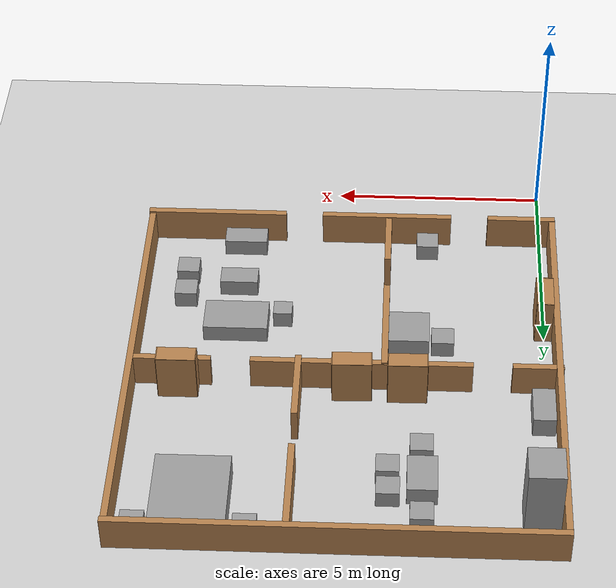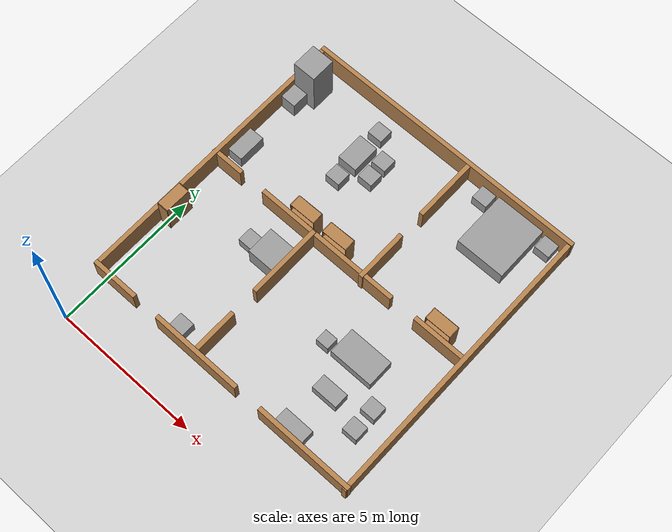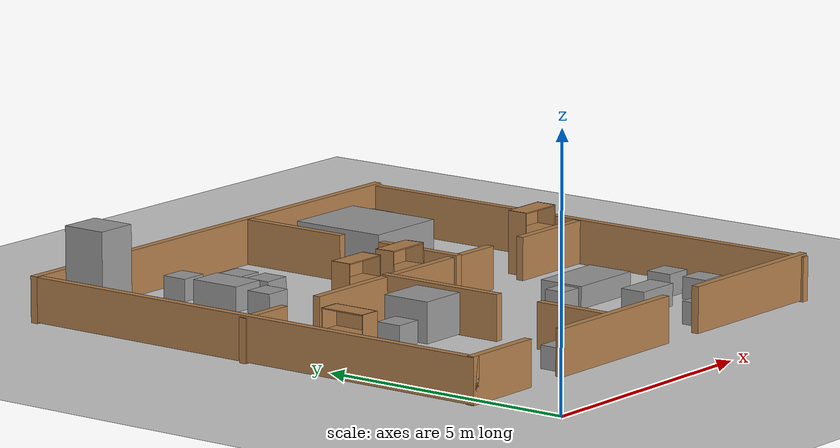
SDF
<sdf version="1.7">
 <world name="default">
  <light name="sun" type="directional">
   <pose>0 0 10 0 -0 0</pose>
   <diffuse>0.8 0.8 0.8 1</diffuse>
   <specular>0.2 0.2 0.2 1</specular>
   <attenuation>
    <range>1000</range>
    <constant>0.9</constant>
    <linear>0.01</linear>
    <quadratic>0.001</quadratic>
   </attenuation>
   <direction>-0.5 0.1 -0.9</direction>
   <spot><inner_angle>0</inner_angle><outer_angle>0</outer_angle><falloff>0</falloff></spot>
  </light>
  <model name="ground_plane">
   <static>1</static>
   <link name="link">
    <collision name="collision">
     <geometry><plane><normal>0 0 1</normal><size>100 100</size></plane></geometry>
     <surface>
      <contact><collide_bitmask>65535</collide_bitmask></contact>
      <friction><ode><mu>100</mu><mu2>50</mu2></ode></friction>
     </surface>
    </collision>
    <visual name="visual">
     <cast_shadows>0</cast_shadows>
     <geometry><plane><normal>0 0 1</normal><size>100 100</size></plane></geometry>
     <material>
      <script><uri>file://media/materials/scripts/gazebo.material</uri><name>Gazebo/Grey</name></script>
     </material>
    </visual>
   </link>
  </model>
  <gravity>0 0 -9.8</gravity>
  <magnetic_field>6e-06 2.3e-05 -4.2e-05</magnetic_field>
  <atmosphere type="adiabatic"/>
  <physics type="ode">
   <max_step_size>0.001</max_step_size>
   <real_time_factor>1</real_time_factor>
   <real_time_update_rate>1000</real_time_update_rate>
  </physics>
  <scene><ambient>0.4 0.4 0.4 1</ambient><background>0.7 0.7 0.7 1</background><shadows>1</shadows></scene>
  <spherical_coordinates>
   <surface_model>EARTH_WGS84</surface_model>
   <latitude_deg>0</latitude_deg>
   <longitude_deg>0</longitude_deg>
   <elevation>0</elevation>
   <heading_deg>0</heading_deg>
  </spherical_coordinates>
  <model name="bookshelf">
   <static>1</static>
   <link name="link">
    <inertial><mass>1</mass></inertial>
    <collision name="back">
     <pose>0 0.005 0.6 0 -0 0</pose>
     <geometry><box><size>0.9 0.01 1.2</size></box></geometry>
    </collision>
    <visual name="visual1">
     <pose>0 0.005 0.6 0 -0 0</pose>
     <geometry><box><size>0.9 0.01 1.2</size></box></geometry>
     <material>
      <script><uri>file://media/materials/scripts/gazebo.material</uri><name>Gazebo/Wood</name></script>
     </material>
    </visual>
    <collision name="left_side">
     <pose>0.45 -0.195 0.6 0 -0 0</pose>
     <geometry><box><size>0.02 0.4 1.2</size></box></geometry>
    </collision>
    <visual name="visual2">
     <pose>0.45 -0.195 0.6 0 -0 0</pose>
     <geometry><box><size>0.02 0.4 1.2</size></box></geometry>
     <material>
      <script><uri>file://media/materials/scripts/gazebo.material</uri><name>Gazebo/Wood</name></script>
     </material>
    </visual>
    <collision name="right_side">
     <pose>-0.45 -0.195 0.6 0 -0 0</pose>
     <geometry><box><size>0.02 0.4 1.2</size></box></geometry>
    </collision>
    <visual name="visual3">
     <pose>-0.45 -0.195 0.6 0 -0 0</pose>
     <geometry><box><size>0.02 0.4 1.2</size></box></geometry>
     <material>
      <script><uri>file://media/materials/scripts/gazebo.material</uri><name>Gazebo/Wood</name></script>
     </material>
    </visual>
    <collision name="bottom">
     <pose>0 -0.195 0.03 0 -0 0</pose>
     <geometry><box><size>0.88 0.4 0.06</size></box></geometry>
    </collision>
    <visual name="visual4">
     <pose>0 -0.195 0.03 0 -0 0</pose>
     <geometry><box><size>0.88 0.4 0.06</size></box></geometry>
     <material>
      <script><uri>file://media/materials/scripts/gazebo.material</uri><name>Gazebo/Wood</name></script>
     </material>
    </visual>
    <collision name="top">
     <pose>0 -0.195 1.19 0 -0 0</pose>
     <geometry><box><size>0.88 0.4 0.02</size></box></geometry>
    </collision>
    <visual name="visual5">
     <pose>0 -0.195 1.19 0 -0 0</pose>
     <geometry><box><size>0.88 0.4 0.02</size></box></geometry>
     <material>
      <script><uri>file://media/materials/scripts/gazebo.material</uri><name>Gazebo/Wood</name></script>
     </material>
    </visual>
    <collision name="low_shelf">
     <pose>0 -0.195 0.43 0 -0 0</pose>
     <geometry><box><size>0.88 0.4 0.02</size></box></geometry>
    </collision>
    <visual name="visual6">
     <pose>0 -0.195 0.43 0 -0 0</pose>
     <geometry><box><size>0.88 0.4 0.02</size></box></geometry>
     <material>
      <script><uri>file://media/materials/scripts/gazebo.material</uri><name>Gazebo/Wood</name></script>
     </material>
    </visual>
    <collision name="high_shelf">
     <pose>0 -0.195 0.8 0 -0 0</pose>
     <geometry><box><size>0.88 0.4 0.02</size></box></geometry>
    </collision>
    <visual name="visual7">
     <pose>0 -0.195 0.8 0 -0 0</pose>
     <geometry><box><size>0.88 0.4 0.02</size></box></geometry>
     <material>
      <script><uri>file://media/materials/scripts/gazebo.material</uri><name>Gazebo/Wood</name></script>
     </material>
    </visual>
   </link>
   <pose>0.222394 4.5972 0 0 -0 -1.57789</pose>
  </model>
  <model name="bookshelf_clone">
   <static>1</static>
   <link name="link">
    <inertial><mass>1</mass></inertial>
    <collision name="back">
     <pose>0 0.005 0.6 0 -0 0</pose>
     <geometry><box><size>0.9 0.01 1.2</size></box></geometry>
    </collision>
    <visual name="visual1">
     <pose>0 0.005 0.6 0 -0 0</pose>
     <geometry><box><size>0.9 0.01 1.2</size></box></geometry>
     <material>
      <script><uri>file://media/materials/scripts/gazebo.material</uri><name>Gazebo/Wood</name></script>
     </material>
    </visual>
    <collision name="left_side">
     <pose>0.45 -0.195 0.6 0 -0 0</pose>
     <geometry><box><size>0.02 0.4 1.2</size></box></geometry>
    </collision>
    <visual name="visual2">
     <pose>0.45 -0.195 0.6 0 -0 0</pose>
     <geometry><box><size>0.02 0.4 1.2</size></box></geometry>
     <material>
      <script><uri>file://media/materials/scripts/gazebo.material</uri><name>Gazebo/Wood</name></script>
     </material>
    </visual>
    <collision name="right_side">
     <pose>-0.45 -0.195 0.6 0 -0 0</pose>
     <geometry><box><size>0.02 0.4 1.2</size></box></geometry>
    </collision>
    <visual name="visual3">
     <pose>-0.45 -0.195 0.6 0 -0 0</pose>
     <geometry><box><size>0.02 0.4 1.2</size></box></geometry>
     <material>
      <script><uri>file://media/materials/scripts/gazebo.material</uri><name>Gazebo/Wood</name></script>
     </material>
    </visual>
    <collision name="bottom">
     <pose>0 -0.195 0.03 0 -0 0</pose>
     <geometry><box><size>0.88 0.4 0.06</size></box></geometry>
    </collision>
    <visual name="visual4">
     <pose>0 -0.195 0.03 0 -0 0</pose>
     <geometry><box><size>0.88 0.4 0.06</size></box></geometry>
     <material>
      <script><uri>file://media/materials/scripts/gazebo.material</uri><name>Gazebo/Wood</name></script>
     </material>
    </visual>
    <collision name="top">
     <pose>0 -0.195 1.19 0 -0 0</pose>
     <geometry><box><size>0.88 0.4 0.02</size></box></geometry>
    </collision>
    <visual name="visual5">
     <pose>0 -0.195 1.19 0 -0 0</pose>
     <geometry><box><size>0.88 0.4 0.02</size></box></geometry>
     <material>
      <script><uri>file://media/materials/scripts/gazebo.material</uri><name>Gazebo/Wood</name></script>
     </material>
    </visual>
    <collision name="low_shelf">
     <pose>0 -0.195 0.43 0 -0 0</pose>
     <geometry><box><size>0.88 0.4 0.02</size></box></geometry>
    </collision>
    <visual name="visual6">
     <pose>0 -0.195 0.43 0 -0 0</pose>
     <geometry><box><size>0.88 0.4 0.02</size></box></geometry>
     <material>
      <script><uri>file://media/materials/scripts/gazebo.material</uri><name>Gazebo/Wood</name></script>
     </material>
    </visual>
    <collision name="high_shelf">
     <pose>0 -0.195 0.8 0 -0 0</pose>
     <geometry><box><size>0.88 0.4 0.02</size></box></geometry>
    </collision>
    <visual name="visual7">
     <pose>0 -0.195 0.8 0 -0 0</pose>
     <geometry><box><size>0.88 0.4 0.02</size></box></geometry>
     <material>
      <script><uri>file://media/materials/scripts/gazebo.material</uri><name>Gazebo/Wood</name></script>
     </material>
    </visual>
   </link>
   <pose>3.20421 7.1574 0 0 -0 0.011143</pose>
  </model>
  <model name="bookshelf_clone_0">
   <static>1</static>
   <link name="link">
    <inertial><mass>1</mass></inertial>
    <collision name="back">
     <pose>0 0.005 0.6 0 -0 0</pose>
     <geometry><box><size>0.9 0.01 1.2</size></box></geometry>
    </collision>
    <visual name="visual1">
     <pose>0 0.005 0.6 0 -0 0</pose>
     <geometry><box><size>0.9 0.01 1.2</size></box></geometry>
     <material>
      <script><uri>file://media/materials/scripts/gazebo.material</uri><name>Gazebo/Wood</name></script>
     </material>
    </visual>
    <collision name="left_side">
     <pose>0.45 -0.195 0.6 0 -0 0</pose>
     <geometry><box><size>0.02 0.4 1.2</size></box></geometry>
    </collision>
    <visual name="visual2">
     <pose>0.45 -0.195 0.6 0 -0 0</pose>
     <geometry><box><size>0.02 0.4 1.2</size></box></geometry>
     <material>
      <script><uri>file://media/materials/scripts/gazebo.material</uri><name>Gazebo/Wood</name></script>
     </material>
    </visual>
    <collision name="right_side">
     <pose>-0.45 -0.195 0.6 0 -0 0</pose>
     <geometry><box><size>0.02 0.4 1.2</size></box></geometry>
    </collision>
    <visual name="visual3">
     <pose>-0.45 -0.195 0.6 0 -0 0</pose>
     <geometry><box><size>0.02 0.4 1.2</size></box></geometry>
     <material>
      <script><uri>file://media/materials/scripts/gazebo.material</uri><name>Gazebo/Wood</name></script>
     </material>
    </visual>
    <collision name="bottom">
     <pose>0 -0.195 0.03 0 -0 0</pose>
     <geometry><box><size>0.88 0.4 0.06</size></box></geometry>
    </collision>
    <visual name="visual4">
     <pose>0 -0.195 0.03 0 -0 0</pose>
     <geometry><box><size>0.88 0.4 0.06</size></box></geometry>
     <material>
      <script><uri>file://media/materials/scripts/gazebo.material</uri><name>Gazebo/Wood</name></script>
     </material>
    </visual>
    <collision name="top">
     <pose>0 -0.195 1.19 0 -0 0</pose>
     <geometry><box><size>0.88 0.4 0.02</size></box></geometry>
    </collision>
    <visual name="visual5">
     <pose>0 -0.195 1.19 0 -0 0</pose>
     <geometry><box><size>0.88 0.4 0.02</size></box></geometry>
     <material>
      <script><uri>file://media/materials/scripts/gazebo.material</uri><name>Gazebo/Wood</name></script>
     </material>
    </visual>
    <collision name="low_shelf">
     <pose>0 -0.195 0.43 0 -0 0</pose>
     <geometry><box><size>0.88 0.4 0.02</size></box></geometry>
    </collision>
    <visual name="visual6">
     <pose>0 -0.195 0.43 0 -0 0</pose>
     <geometry><box><size>0.88 0.4 0.02</size></box></geometry>
     <material>
      <script><uri>file://media/materials/scripts/gazebo.material</uri><name>Gazebo/Wood</name></script>
     </material>
    </visual>
    <collision name="high_shelf">
     <pose>0 -0.195 0.8 0 -0 0</pose>
     <geometry><box><size>0.88 0.4 0.02</size></box></geometry>
    </collision>
    <visual name="visual7">
     <pose>0 -0.195 0.8 0 -0 0</pose>
     <geometry><box><size>0.88 0.4 0.02</size></box></geometry>
     <material>
      <script><uri>file://media/materials/scripts/gazebo.material</uri><name>Gazebo/Wood</name></script>
     </material>
    </visual>
   </link>
   <pose>4.47359 7.13831 -0.006508 -0.017087 0.000419 0.020797</pose>
  </model>
  <model name="unit_box">
   <link name="link">
    <inertial>
     <mass>1</mass>
     <inertia>
      <ixx>0.166667</ixx>
      <ixy>0</ixy>
      <ixz>0</ixz>
      <iyy>0.166667</iyy>
      <iyz>0</iyz>
      <izz>0.166667</izz>
     </inertia>
    </inertial>
    <visual name="visual">
     <geometry><box><size>1.68417 1.93569 0.590711</size></box></geometry>
     <material>
      <script><name>Gazebo/Grey</name><uri>file://media/materials/scripts/gazebo.material</uri></script>
      <shader type="pixel"><normal_map>__default__</normal_map></shader>
      <ambient>0.933 0.933 0.925 1</ambient>
      <diffuse>0.7 0.7 0.7 1</diffuse>
      <specular>0.01 0.01 0.01 1</specular>
      <emissive>0 0 0 1</emissive>
     </material>
    </visual>
    <collision name="collision">
     <geometry><box><size>1.68417 1.93569 0.590711</size></box></geometry>
     <surface>
      <friction>
       <ode><mu>1</mu><mu2>1</mu2><fdir1>0 0 0</fdir1><slip1>0</slip1><slip2>0</slip2></ode>
       <torsional>
        <coefficient>1</coefficient>
        <patch_radius>0</patch_radius>
        <surface_radius>0</surface_radius>
        <use_patch_radius>1</use_patch_radius>
        <ode><slip>0</slip></ode>
       </torsional>
      </friction>
      <bounce><restitution_coefficient>0</restitution_coefficient><threshold>1e+06</threshold></bounce>
      <contact>
       <collide_without_contact>0</collide_without_contact>
       <collide_without_contact_bitmask>1</collide_without_contact_bitmask>
       <collide_bitmask>1</collide_bitmask>
       <ode>
        <soft_cfm>0</soft_cfm>
        <soft_erp>0.2</soft_erp>
        <kp>1e+13</kp>
        <kd>1</kd>
        <max_vel>0.01</max_vel>
        <min_depth>0</min_depth>
       </ode>
       <bullet>
        <split_impulse>1</split_impulse>
        <split_impulse_penetration_threshold>-0.01</split_impulse_penetration_threshold>
        <soft_cfm>0</soft_cfm>
        <soft_erp>0.2</soft_erp>
        <kp>1e+13</kp>
        <kd>1</kd>
       </bullet>
      </contact>
     </surface>
    </collision>
   </link>
   <static>0</static>
   <pose>7.86164 10.4166 0.295328 2.8e-05 -0 0.001435</pose>
  </model>
  <model name="unit_box_clone">
   <link name="link">
    <inertial>
     <mass>1</mass>
     <inertia>
      <ixx>0.166667</ixx>
      <ixy>0</ixy>
      <ixz>0</ixz>
      <iyy>0.166667</iyy>
      <iyz>0</iyz>
      <izz>0.166667</izz>
     </inertia>
    </inertial>
    <visual name="visual">
     <geometry><box><size>0.525272 0.502179 0.423961</size></box></geometry>
     <material>
      <script><name>Gazebo/Grey</name><uri>file://media/materials/scripts/gazebo.material</uri></script>
      <shader type="pixel"><normal_map>__default__</normal_map></shader>
      <ambient>0.933 0.933 0.925 1</ambient>
      <diffuse>0.7 0.7 0.7 1</diffuse>
      <specular>0.01 0.01 0.01 1</specular>
      <emissive>0 0 0 1</emissive>
     </material>
    </visual>
    <collision name="collision">
     <geometry><box><size>0.525272 0.502179 0.423961</size></box></geometry>
     <surface>
      <friction>
       <ode><mu>1</mu><mu2>1</mu2><fdir1>0 0 0</fdir1><slip1>0</slip1><slip2>0</slip2></ode>
       <torsional>
        <coefficient>1</coefficient>
        <patch_radius>0</patch_radius>
        <surface_radius>0</surface_radius>
        <use_patch_radius>1</use_patch_radius>
        <ode><slip>0</slip></ode>
       </torsional>
      </friction>
      <bounce><restitution_coefficient>0</restitution_coefficient><threshold>1e+06</threshold></bounce>
      <contact>
       <collide_without_contact>0</collide_without_contact>
       <collide_without_contact_bitmask>1</collide_without_contact_bitmask>
       <collide_bitmask>1</collide_bitmask>
       <ode>
        <soft_cfm>0</soft_cfm>
        <soft_erp>0.2</soft_erp>
        <kp>1e+13</kp>
        <kd>1</kd>
        <max_vel>0.01</max_vel>
        <min_depth>0</min_depth>
       </ode>
       <bullet>
        <split_impulse>1</split_impulse>
        <split_impulse_penetration_threshold>-0.01</split_impulse_penetration_threshold>
        <soft_cfm>0</soft_cfm>
        <soft_erp>0.2</soft_erp>
        <kp>1e+13</kp>
        <kd>1</kd>
       </bullet>
      </contact>
     </surface>
    </collision>
   </link>
   <static>0</static>
   <pose>6.63512 11.1676 0.21198 0 0 -6e-06</pose>
  </model>
  <model name="unit_box_clone_0">
   <link name="link">
    <inertial>
     <mass>1</mass>
     <inertia>
      <ixx>0.166667</ixx>
      <ixy>0</ixy>
      <ixz>0</ixz>
      <iyy>0.166667</iyy>
      <iyz>0</iyz>
      <izz>0.166667</izz>
     </inertia>
    </inertial>
    <visual name="visual">
     <geometry><box><size>0.525272 0.502179 0.423961</size></box></geometry>
     <material>
      <script><name>Gazebo/Grey</name><uri>file://media/materials/scripts/gazebo.material</uri></script>
      <shader type="pixel"><normal_map>__default__</normal_map></shader>
      <ambient>0.933 0.933 0.925 1</ambient>
      <diffuse>0.7 0.7 0.7 1</diffuse>
      <specular>0.01 0.01 0.01 1</specular>
      <emissive>0 0 0 1</emissive>
     </material>
    </visual>
    <collision name="collision">
     <geometry><box><size>0.525272 0.502179 0.423961</size></box></geometry>
     <surface>
      <friction>
       <ode><mu>1</mu><mu2>1</mu2><fdir1>0 0 0</fdir1><slip1>0</slip1><slip2>0</slip2></ode>
       <torsional>
        <coefficient>1</coefficient>
        <patch_radius>0</patch_radius>
        <surface_radius>0</surface_radius>
        <use_patch_radius>1</use_patch_radius>
        <ode><slip>0</slip></ode>
       </torsional>
      </friction>
      <bounce><restitution_coefficient>0</restitution_coefficient><threshold>1e+06</threshold></bounce>
      <contact>
       <collide_without_contact>0</collide_without_contact>
       <collide_without_contact_bitmask>1</collide_without_contact_bitmask>
       <collide_bitmask>1</collide_bitmask>
       <ode>
        <soft_cfm>0</soft_cfm>
        <soft_erp>0.2</soft_erp>
        <kp>1e+13</kp>
        <kd>1</kd>
        <max_vel>0.01</max_vel>
        <min_depth>0</min_depth>
       </ode>
       <bullet>
        <split_impulse>1</split_impulse>
        <split_impulse_penetration_threshold>-0.01</split_impulse_penetration_threshold>
        <soft_cfm>0</soft_cfm>
        <soft_erp>0.2</soft_erp>
        <kp>1e+13</kp>
        <kd>1</kd>
       </bullet>
      </contact>
     </surface>
    </collision>
   </link>
   <static>0</static>
   <pose>2.77764 2.06187 0.21198 0 0 -2.3e-05</pose>
  </model>
  <model name="bookshelf_clone_0_clone">
   <static>1</static>
   <link name="link">
    <inertial><mass>1</mass></inertial>
    <collision name="back">
     <pose>0 0.005 0.6 0 -0 0</pose>
     <geometry><box><size>0.9 0.01 1.2</size></box></geometry>
    </collision>
    <visual name="visual1">
     <pose>0 0.005 0.6 0 -0 0</pose>
     <geometry><box><size>0.9 0.01 1.2</size></box></geometry>
     <material>
      <script><uri>file://media/materials/scripts/gazebo.material</uri><name>Gazebo/Wood</name></script>
     </material>
    </visual>
    <collision name="left_side">
     <pose>0.45 -0.195 0.6 0 -0 0</pose>
     <geometry><box><size>0.02 0.4 1.2</size></box></geometry>
    </collision>
    <visual name="visual2">
     <pose>0.45 -0.195 0.6 0 -0 0</pose>
     <geometry><box><size>0.02 0.4 1.2</size></box></geometry>
     <material>
      <script><uri>file://media/materials/scripts/gazebo.material</uri><name>Gazebo/Wood</name></script>
     </material>
    </visual>
    <collision name="right_side">
     <pose>-0.45 -0.195 0.6 0 -0 0</pose>
     <geometry><box><size>0.02 0.4 1.2</size></box></geometry>
    </collision>
    <visual name="visual3">
     <pose>-0.45 -0.195 0.6 0 -0 0</pose>
     <geometry><box><size>0.02 0.4 1.2</size></box></geometry>
     <material>
      <script><uri>file://media/materials/scripts/gazebo.material</uri><name>Gazebo/Wood</name></script>
     </material>
    </visual>
    <collision name="bottom">
     <pose>0 -0.195 0.03 0 -0 0</pose>
     <geometry><box><size>0.88 0.4 0.06</size></box></geometry>
    </collision>
    <visual name="visual4">
     <pose>0 -0.195 0.03 0 -0 0</pose>
     <geometry><box><size>0.88 0.4 0.06</size></box></geometry>
     <material>
      <script><uri>file://media/materials/scripts/gazebo.material</uri><name>Gazebo/Wood</name></script>
     </material>
    </visual>
    <collision name="top">
     <pose>0 -0.195 1.19 0 -0 0</pose>
     <geometry><box><size>0.88 0.4 0.02</size></box></geometry>
    </collision>
    <visual name="visual5">
     <pose>0 -0.195 1.19 0 -0 0</pose>
     <geometry><box><size>0.88 0.4 0.02</size></box></geometry>
     <material>
      <script><uri>file://media/materials/scripts/gazebo.material</uri><name>Gazebo/Wood</name></script>
     </material>
    </visual>
    <collision name="low_shelf">
     <pose>0 -0.195 0.43 0 -0 0</pose>
     <geometry><box><size>0.88 0.4 0.02</size></box></geometry>
    </collision>
    <visual name="visual6">
     <pose>0 -0.195 0.43 0 -0 0</pose>
     <geometry><box><size>0.88 0.4 0.02</size></box></geometry>
     <material>
      <script><uri>file://media/materials/scripts/gazebo.material</uri><name>Gazebo/Wood</name></script>
     </material>
    </visual>
    <collision name="high_shelf">
     <pose>0 -0.195 0.8 0 -0 0</pose>
     <geometry><box><size>0.88 0.4 0.02</size></box></geometry>
    </collision>
    <visual name="visual7">
     <pose>0 -0.195 0.8 0 -0 0</pose>
     <geometry><box><size>0.88 0.4 0.02</size></box></geometry>
     <material>
      <script><uri>file://media/materials/scripts/gazebo.material</uri><name>Gazebo/Wood</name></script>
     </material>
    </visual>
   </link>
   <pose>8.46497 7.1577 0 0 -0 0.007205</pose>
  </model>
  <model name="unit_box_clone_clone">
   <link name="link">
    <inertial>
     <mass>1</mass>
     <inertia>
      <ixx>0.166667</ixx>
      <ixy>0</ixy>
      <ixz>0</ixz>
      <iyy>0.166667</iyy>
      <iyz>0</iyz>
      <izz>0.166667</izz>
     </inertia>
    </inertial>
    <visual name="visual">
     <geometry><box><size>0.808451 0.858287 1.84502</size></box></geometry>
     <material>
      <script><name>Gazebo/Grey</name><uri>file://media/materials/scripts/gazebo.material</uri></script>
      <shader type="pixel"><normal_map>__default__</normal_map></shader>
      <ambient>0.933 0.933 0.925 1</ambient>
      <diffuse>0.7 0.7 0.7 1</diffuse>
      <specular>0.01 0.01 0.01 1</specular>
      <emissive>0 0 0 1</emissive>
     </material>
    </visual>
    <collision name="collision">
     <geometry><box><size>0.808451 0.858287 1.84502</size></box></geometry>
     <surface>
      <friction>
       <ode><mu>1</mu><mu2>1</mu2><fdir1>0 0 0</fdir1><slip1>0</slip1><slip2>0</slip2></ode>
       <torsional>
        <coefficient>1</coefficient>
        <patch_radius>0</patch_radius>
        <surface_radius>0</surface_radius>
        <use_patch_radius>1</use_patch_radius>
        <ode><slip>0</slip></ode>
       </torsional>
      </friction>
      <bounce><restitution_coefficient>0</restitution_coefficient><threshold>1e+06</threshold></bounce>
      <contact>
       <collide_without_contact>0</collide_without_contact>
       <collide_without_contact_bitmask>1</collide_without_contact_bitmask>
       <collide_bitmask>1</collide_bitmask>
       <ode>
        <soft_cfm>0</soft_cfm>
        <soft_erp>0.2</soft_erp>
        <kp>1e+13</kp>
        <kd>1</kd>
        <max_vel>0.01</max_vel>
        <min_depth>0</min_depth>
       </ode>
       <bullet>
        <split_impulse>1</split_impulse>
        <split_impulse_penetration_threshold>-0.01</split_impulse_penetration_threshold>
        <soft_cfm>0</soft_cfm>
        <soft_erp>0.2</soft_erp>
        <kp>1e+13</kp>
        <kd>1</kd>
       </bullet>
      </contact>
     </surface>
    </collision>
   </link>
   <static>0</static>
   <pose>0.247629 10.497 0.922507 -3e-06 3e-06 -0.000221</pose>
  </model>
  <model name="unit_box_clone_clone_0">
   <link name="link">
    <inertial>
     <mass>1</mass>
     <inertia>
      <ixx>0.166667</ixx>
      <ixy>0</ixy>
      <ixz>0</ixz>
      <iyy>0.166667</iyy>
      <iyz>0</iyz>
      <izz>0.166667</izz>
     </inertia>
    </inertial>
    <visual name="visual">
     <geometry><box><size>0.525272 0.583453 0.630859</size></box></geometry>
     <material>
      <script><name>Gazebo/Grey</name><uri>file://media/materials/scripts/gazebo.material</uri></script>
      <shader type="pixel"><normal_map>__default__</normal_map></shader>
      <ambient>0.933 0.933 0.925 1</ambient>
      <diffuse>0.7 0.7 0.7 1</diffuse>
      <specular>0.01 0.01 0.01 1</specular>
      <emissive>0 0 0 1</emissive>
     </material>
    </visual>
    <collision name="collision">
     <geometry><box><size>0.525272 0.583453 0.630859</size></box></geometry>
     <surface>
      <friction>
       <ode><mu>1</mu><mu2>1</mu2><fdir1>0 0 0</fdir1><slip1>0</slip1><slip2>0</slip2></ode>
       <torsional>
        <coefficient>1</coefficient>
        <patch_radius>0</patch_radius>
        <surface_radius>0</surface_radius>
        <use_patch_radius>1</use_patch_radius>
        <ode><slip>0</slip></ode>
       </torsional>
      </friction>
      <bounce><restitution_coefficient>0</restitution_coefficient><threshold>1e+06</threshold></bounce>
      <contact>
       <collide_without_contact>0</collide_without_contact>
       <collide_without_contact_bitmask>1</collide_without_contact_bitmask>
       <collide_bitmask>1</collide_bitmask>
       <ode>
        <soft_cfm>0</soft_cfm>
        <soft_erp>0.2</soft_erp>
        <kp>1e+13</kp>
        <kd>1</kd>
        <max_vel>0.01</max_vel>
        <min_depth>0</min_depth>
       </ode>
       <bullet>
        <split_impulse>1</split_impulse>
        <split_impulse_penetration_threshold>-0.01</split_impulse_penetration_threshold>
        <soft_cfm>0</soft_cfm>
        <soft_erp>0.2</soft_erp>
        <kp>1e+13</kp>
        <kd>1</kd>
       </bullet>
      </contact>
     </surface>
    </collision>
   </link>
   <static>0</static>
   <pose>0.097615 9.77175 0.31543 0 0 -6e-06</pose>
  </model>
  <model name="unit_box_clone_clone_1">
   <link name="link">
    <inertial>
     <mass>1</mass>
     <inertia>
      <ixx>0.166667</ixx>
      <ixy>0</ixy>
      <ixz>0</ixz>
      <iyy>0.166667</iyy>
      <iyz>0</iyz>
      <izz>0.166667</izz>
     </inertia>
    </inertial>
    <visual name="visual">
     <geometry><box><size>0.525272 0.97954 0.509969</size></box></geometry>
     <material>
      <script><name>Gazebo/Grey</name><uri>file://media/materials/scripts/gazebo.material</uri></script>
      <shader type="pixel"><normal_map>__default__</normal_map></shader>
      <ambient>0.933 0.933 0.925 1</ambient>
      <diffuse>0.7 0.7 0.7 1</diffuse>
      <specular>0.01 0.01 0.01 1</specular>
      <emissive>0 0 0 1</emissive>
     </material>
    </visual>
    <collision name="collision">
     <geometry><box><size>0.525272 0.97954 0.509969</size></box></geometry>
     <surface>
      <friction>
       <ode><mu>1</mu><mu2>1</mu2><fdir1>0 0 0</fdir1><slip1>0</slip1><slip2>0</slip2></ode>
       <torsional>
        <coefficient>1</coefficient>
        <patch_radius>0</patch_radius>
        <surface_radius>0</surface_radius>
        <use_patch_radius>1</use_patch_radius>
        <ode><slip>0</slip></ode>
       </torsional>
      </friction>
      <bounce><restitution_coefficient>0</restitution_coefficient><threshold>1e+06</threshold></bounce>
      <contact>
       <collide_without_contact>0</collide_without_contact>
       <collide_without_contact_bitmask>1</collide_without_contact_bitmask>
       <collide_bitmask>1</collide_bitmask>
       <ode>
        <soft_cfm>0</soft_cfm>
        <soft_erp>0.2</soft_erp>
        <kp>1e+13</kp>
        <kd>1</kd>
        <max_vel>0.01</max_vel>
        <min_depth>0</min_depth>
       </ode>
       <bullet>
        <split_impulse>1</split_impulse>
        <split_impulse_penetration_threshold>-0.01</split_impulse_penetration_threshold>
        <soft_cfm>0</soft_cfm>
        <soft_erp>0.2</soft_erp>
        <kp>1e+13</kp>
        <kd>1</kd>
       </bullet>
      </contact>
     </surface>
    </collision>
   </link>
   <static>0</static>
   <pose>0.106653 7.572 0.254985 -0 -0 -4e-06</pose>
  </model>
  <model name="unit_box_clone_clone_2">
   <link name="link">
    <inertial>
     <mass>1</mass>
     <inertia>
      <ixx>0.166667</ixx>
      <ixy>0</ixy>
      <ixz>0</ixz>
      <iyy>0.166667</iyy>
      <iyz>0</iyz>
      <izz>0.166667</izz>
     </inertia>
    </inertial>
    <visual name="visual">
     <geometry><box><size>0.525272 0.502179 0.423961</size></box></geometry>
     <material>
      <script><name>Gazebo/Grey</name><uri>file://media/materials/scripts/gazebo.material</uri></script>
      <shader type="pixel"><normal_map>__default__</normal_map></shader>
      <ambient>0.933 0.933 0.925 1</ambient>
      <diffuse>0.7 0.7 0.7 1</diffuse>
      <specular>0.01 0.01 0.01 1</specular>
      <emissive>0 0 0 1</emissive>
     </material>
    </visual>
    <collision name="collision">
     <geometry><box><size>0.525272 0.502179 0.423961</size></box></geometry>
     <surface>
      <friction>
       <ode><mu>1</mu><mu2>1</mu2><fdir1>0 0 0</fdir1><slip1>0</slip1><slip2>0</slip2></ode>
       <torsional>
        <coefficient>1</coefficient>
        <patch_radius>0</patch_radius>
        <surface_radius>0</surface_radius>
        <use_patch_radius>1</use_patch_radius>
        <ode><slip>0</slip></ode>
       </torsional>
      </friction>
      <bounce><restitution_coefficient>0</restitution_coefficient><threshold>1e+06</threshold></bounce>
      <contact>
       <collide_without_contact>0</collide_without_contact>
       <collide_without_contact_bitmask>1</collide_without_contact_bitmask>
       <collide_bitmask>1</collide_bitmask>
       <ode>
        <soft_cfm>0</soft_cfm>
        <soft_erp>0.2</soft_erp>
        <kp>1e+13</kp>
        <kd>1</kd>
        <max_vel>0.01</max_vel>
        <min_depth>0</min_depth>
       </ode>
       <bullet>
        <split_impulse>1</split_impulse>
        <split_impulse_penetration_threshold>-0.01</split_impulse_penetration_threshold>
        <soft_cfm>0</soft_cfm>
        <soft_erp>0.2</soft_erp>
        <kp>1e+13</kp>
        <kd>1</kd>
       </bullet>
      </contact>
     </surface>
    </collision>
   </link>
   <static>0</static>
   <pose>8.57018 3.15894 0.21198 0 0 -6e-06</pose>
  </model>
  <model name="unit_box_clone_clone_3">
   <link name="link">
    <inertial>
     <mass>1</mass>
     <inertia>
      <ixx>0.166667</ixx>
      <ixy>0</ixy>
      <ixz>0</ixz>
      <iyy>0.166667</iyy>
      <iyz>0</iyz>
      <izz>0.166667</izz>
     </inertia>
    </inertial>
    <visual name="visual">
     <geometry><box><size>1.51241 0.912395 0.423961</size></box></geometry>
     <material>
      <script><name>Gazebo/Grey</name><uri>file://media/materials/scripts/gazebo.material</uri></script>
      <shader type="pixel"><normal_map>__default__</normal_map></shader>
      <ambient>0.933 0.933 0.925 1</ambient>
      <diffuse>0.7 0.7 0.7 1</diffuse>
      <specular>0.01 0.01 0.01 1</specular>
      <emissive>0 0 0 1</emissive>
     </material>
    </visual>
    <collision name="collision">
     <geometry><box><size>1.51241 0.912395 0.423961</size></box></geometry>
     <surface>
      <friction>
       <ode><mu>1</mu><mu2>1</mu2><fdir1>0 0 0</fdir1><slip1>0</slip1><slip2>0</slip2></ode>
       <torsional>
        <coefficient>1</coefficient>
        <patch_radius>0</patch_radius>
        <surface_radius>0</surface_radius>
        <use_patch_radius>1</use_patch_radius>
        <ode><slip>0</slip></ode>
       </torsional>
      </friction>
      <bounce><restitution_coefficient>0</restitution_coefficient><threshold>1e+06</threshold></bounce>
      <contact>
       <collide_without_contact>0</collide_without_contact>
       <collide_without_contact_bitmask>1</collide_without_contact_bitmask>
       <collide_bitmask>1</collide_bitmask>
       <ode>
        <soft_cfm>0</soft_cfm>
        <soft_erp>0.2</soft_erp>
        <kp>1e+13</kp>
        <kd>1</kd>
        <max_vel>0.01</max_vel>
        <min_depth>0</min_depth>
       </ode>
       <bullet>
        <split_impulse>1</split_impulse>
        <split_impulse_penetration_threshold>-0.01</split_impulse_penetration_threshold>
        <soft_cfm>0</soft_cfm>
        <soft_erp>0.2</soft_erp>
        <kp>1e+13</kp>
        <kd>1</kd>
       </bullet>
      </contact>
     </surface>
    </collision>
   </link>
   <static>0</static>
   <pose>7.28625 4.84842 0.211975 1e-05 0 -1.5e-05</pose>
  </model>
  <model name="unit_box_clone_clone_4">
   <link name="link">
    <inertial>
     <mass>1</mass>
     <inertia>
      <ixx>0.166667</ixx>
      <ixy>0</ixy>
      <ixz>0</ixz>
      <iyy>0.166667</iyy>
      <iyz>0</iyz>
      <izz>0.166667</izz>
     </inertia>
    </inertial>
    <visual name="visual">
     <geometry><box><size>0.899816 0.502179 0.423961</size></box></geometry>
     <material>
      <script><name>Gazebo/Grey</name><uri>file://media/materials/scripts/gazebo.material</uri></script>
      <shader type="pixel"><normal_map>__default__</normal_map></shader>
      <ambient>0.933 0.933 0.925 1</ambient>
      <diffuse>0.7 0.7 0.7 1</diffuse>
      <specular>0.01 0.01 0.01 1</specular>
      <emissive>0 0 0 1</emissive>
     </material>
    </visual>
    <collision name="collision">
     <geometry><box><size>0.899816 0.502179 0.423961</size></box></geometry>
     <surface>
      <friction>
       <ode><mu>1</mu><mu2>1</mu2><fdir1>0 0 0</fdir1><slip1>0</slip1><slip2>0</slip2></ode>
       <torsional>
        <coefficient>1</coefficient>
        <patch_radius>0</patch_radius>
        <surface_radius>0</surface_radius>
        <use_patch_radius>1</use_patch_radius>
        <ode><slip>0</slip></ode>
       </torsional>
      </friction>
      <bounce><restitution_coefficient>0</restitution_coefficient><threshold>1e+06</threshold></bounce>
      <contact>
       <collide_without_contact>0</collide_without_contact>
       <collide_without_contact_bitmask>1</collide_without_contact_bitmask>
       <collide_bitmask>1</collide_bitmask>
       <ode>
        <soft_cfm>0</soft_cfm>
        <soft_erp>0.2</soft_erp>
        <kp>1e+13</kp>
        <kd>1</kd>
        <max_vel>0.01</max_vel>
        <min_depth>0</min_depth>
       </ode>
       <bullet>
        <split_impulse>1</split_impulse>
        <split_impulse_penetration_threshold>-0.01</split_impulse_penetration_threshold>
        <soft_cfm>0</soft_cfm>
        <soft_erp>0.2</soft_erp>
        <kp>1e+13</kp>
        <kd>1</kd>
       </bullet>
      </contact>
     </surface>
    </collision>
   </link>
   <static>0</static>
   <pose>7.31194 3.48853 0.21198 0 0 -6e-06</pose>
  </model>
  <model name="unit_box_clone_clone_6">
   <link name="link">
    <inertial>
     <mass>1</mass>
     <inertia>
      <ixx>0.166667</ixx>
      <ixy>0</ixy>
      <ixz>0</ixz>
      <iyy>0.166667</iyy>
      <iyz>0</iyz>
      <izz>0.166667</izz>
     </inertia>
    </inertial>
    <visual name="visual">
     <geometry><box><size>0.441981 0.41866 0.423961</size></box></geometry>
     <material>
      <script><name>Gazebo/Grey</name><uri>file://media/materials/scripts/gazebo.material</uri></script>
      <shader type="pixel"><normal_map>__default__</normal_map></shader>
      <ambient>0.933 0.933 0.925 1</ambient>
      <diffuse>0.7 0.7 0.7 1</diffuse>
      <specular>0.01 0.01 0.01 1</specular>
      <emissive>0 0 0 1</emissive>
     </material>
    </visual>
    <collision name="collision">
     <geometry><box><size>0.441981 0.41866 0.423961</size></box></geometry>
     <surface>
      <friction>
       <ode><mu>1</mu><mu2>1</mu2><fdir1>0 0 0</fdir1><slip1>0</slip1><slip2>0</slip2></ode>
       <torsional>
        <coefficient>1</coefficient>
        <patch_radius>0</patch_radius>
        <surface_radius>0</surface_radius>
        <use_patch_radius>1</use_patch_radius>
        <ode><slip>0</slip></ode>
       </torsional>
      </friction>
      <bounce><restitution_coefficient>0</restitution_coefficient><threshold>1e+06</threshold></bounce>
      <contact>
       <collide_without_contact>0</collide_without_contact>
       <collide_without_contact_bitmask>1</collide_without_contact_bitmask>
       <collide_bitmask>1</collide_bitmask>
       <ode>
        <soft_cfm>0</soft_cfm>
        <soft_erp>0.2</soft_erp>
        <kp>1e+13</kp>
        <kd>1</kd>
        <max_vel>0.01</max_vel>
        <min_depth>0</min_depth>
       </ode>
       <bullet>
        <split_impulse>1</split_impulse>
        <split_impulse_penetration_threshold>-0.01</split_impulse_penetration_threshold>
        <soft_cfm>0</soft_cfm>
        <soft_erp>0.2</soft_erp>
        <kp>1e+13</kp>
        <kd>1</kd>
       </bullet>
      </contact>
     </surface>
    </collision>
   </link>
   <static>0</static>
   <pose>6.1965 4.57944 0.21198 0 0 -6e-06</pose>
  </model>
  <model name="unit_box_clone_clone_7">
   <link name="link">
    <inertial>
     <mass>1</mass>
     <inertia>
      <ixx>0.166667</ixx>
      <ixy>0</ixy>
      <ixz>0</ixz>
      <iyy>0.166667</iyy>
      <iyz>0</iyz>
      <izz>0.166667</izz>
     </inertia>
    </inertial>
    <visual name="visual">
     <geometry><box><size>1.0251 0.502179 0.423961</size></box></geometry>
     <material>
      <script><name>Gazebo/Grey</name><uri>file://media/materials/scripts/gazebo.material</uri></script>
      <shader type="pixel"><normal_map>__default__</normal_map></shader>
      <ambient>0.933 0.933 0.925 1</ambient>
      <diffuse>0.7 0.7 0.7 1</diffuse>
      <specular>0.01 0.01 0.01 1</specular>
      <emissive>0 0 0 1</emissive>
     </material>
    </visual>
    <collision name="collision">
     <geometry><box><size>1.0251 0.502179 0.423961</size></box></geometry>
     <surface>
      <friction>
       <ode><mu>1</mu><mu2>1</mu2><fdir1>0 0 0</fdir1><slip1>0</slip1><slip2>0</slip2></ode>
       <torsional>
        <coefficient>1</coefficient>
        <patch_radius>0</patch_radius>
        <surface_radius>0</surface_radius>
        <use_patch_radius>1</use_patch_radius>
        <ode><slip>0</slip></ode>
       </torsional>
      </friction>
      <bounce><restitution_coefficient>0</restitution_coefficient><threshold>1e+06</threshold></bounce>
      <contact>
       <collide_without_contact>0</collide_without_contact>
       <collide_without_contact_bitmask>1</collide_without_contact_bitmask>
       <collide_bitmask>1</collide_bitmask>
       <ode>
        <soft_cfm>0</soft_cfm>
        <soft_erp>0.2</soft_erp>
        <kp>1e+13</kp>
        <kd>1</kd>
        <max_vel>0.01</max_vel>
        <min_depth>0</min_depth>
       </ode>
       <bullet>
        <split_impulse>1</split_impulse>
        <split_impulse_penetration_threshold>-0.01</split_impulse_penetration_threshold>
        <soft_cfm>0</soft_cfm>
        <soft_erp>0.2</soft_erp>
        <kp>1e+13</kp>
        <kd>1</kd>
       </bullet>
      </contact>
     </surface>
    </collision>
   </link>
   <static>0</static>
   <pose>7.24442 2.04094 0.21198 0 -0 2.6e-05</pose>
  </model>
  <model name="unit_box_clone_clone_8">
   <link name="link">
    <inertial>
     <mass>1</mass>
     <inertia>
      <ixx>0.166667</ixx>
      <ixy>0</ixy>
      <ixz>0</ixz>
      <iyy>0.166667</iyy>
      <iyz>0</iyz>
      <izz>0.166667</izz>
     </inertia>
    </inertial>
    <visual name="visual">
     <geometry><box><size>0.525272 0.502179 0.423961</size></box></geometry>
     <material>
      <script><name>Gazebo/Grey</name><uri>file://media/materials/scripts/gazebo.material</uri></script>
      <shader type="pixel"><normal_map>__default__</normal_map></shader>
      <ambient>0.933 0.933 0.925 1</ambient>
      <diffuse>0.7 0.7 0.7 1</diffuse>
      <specular>0.01 0.01 0.01 1</specular>
      <emissive>0 0 0 1</emissive>
     </material>
    </visual>
    <collision name="collision">
     <geometry><box><size>0.525272 0.502179 0.423961</size></box></geometry>
     <surface>
      <friction>
       <ode><mu>1</mu><mu2>1</mu2><fdir1>0 0 0</fdir1><slip1>0</slip1><slip2>0</slip2></ode>
       <torsional>
        <coefficient>1</coefficient>
        <patch_radius>0</patch_radius>
        <surface_radius>0</surface_radius>
        <use_patch_radius>1</use_patch_radius>
        <ode><slip>0</slip></ode>
       </torsional>
      </friction>
      <bounce><restitution_coefficient>0</restitution_coefficient><threshold>1e+06</threshold></bounce>
      <contact>
       <collide_without_contact>0</collide_without_contact>
       <collide_without_contact_bitmask>1</collide_without_contact_bitmask>
       <collide_bitmask>1</collide_bitmask>
       <ode>
        <soft_cfm>0</soft_cfm>
        <soft_erp>0.2</soft_erp>
        <kp>1e+13</kp>
        <kd>1</kd>
        <max_vel>0.01</max_vel>
        <min_depth>0</min_depth>
       </ode>
       <bullet>
        <split_impulse>1</split_impulse>
        <split_impulse_penetration_threshold>-0.01</split_impulse_penetration_threshold>
        <soft_cfm>0</soft_cfm>
        <soft_erp>0.2</soft_erp>
        <kp>1e+13</kp>
        <kd>1</kd>
       </bullet>
      </contact>
     </surface>
    </collision>
   </link>
   <static>0</static>
   <pose>2.39961 5.38819 0.21198 0 0 -6e-06</pose>
  </model>
  <model name="unit_box_clone_clone_1_clone">
   <link name="link">
    <inertial>
     <mass>1</mass>
     <inertia>
      <ixx>0.166667</ixx>
      <ixy>0</ixy>
      <ixz>0</ixz>
      <iyy>0.166667</iyy>
      <iyz>0</iyz>
      <izz>0.166667</izz>
     </inertia>
    </inertial>
    <visual name="visual">
     <geometry><box><size>0.682472 0.993503 0.47723</size></box></geometry>
     <material>
      <script><name>Gazebo/Grey</name><uri>file://media/materials/scripts/gazebo.material</uri></script>
      <shader type="pixel"><normal_map>__default__</normal_map></shader>
      <ambient>0.933 0.933 0.925 1</ambient>
      <diffuse>0.7 0.7 0.7 1</diffuse>
      <specular>0.01 0.01 0.01 1</specular>
      <emissive>0 0 0 1</emissive>
     </material>
    </visual>
    <collision name="collision">
     <geometry><box><size>0.682472 0.993503 0.47723</size></box></geometry>
     <surface>
      <friction>
       <ode><mu>1</mu><mu2>1</mu2><fdir1>0 0 0</fdir1><slip1>0</slip1><slip2>0</slip2></ode>
       <torsional>
        <coefficient>1</coefficient>
        <patch_radius>0</patch_radius>
        <surface_radius>0</surface_radius>
        <use_patch_radius>1</use_patch_radius>
        <ode><slip>0</slip></ode>
       </torsional>
      </friction>
      <bounce><restitution_coefficient>0</restitution_coefficient><threshold>1e+06</threshold></bounce>
      <contact>
       <collide_without_contact>0</collide_without_contact>
       <collide_without_contact_bitmask>1</collide_without_contact_bitmask>
       <collide_bitmask>1</collide_bitmask>
       <ode>
        <soft_cfm>0</soft_cfm>
        <soft_erp>0.2</soft_erp>
        <kp>1e+13</kp>
        <kd>1</kd>
        <max_vel>0.01</max_vel>
        <min_depth>0</min_depth>
       </ode>
       <bullet>
        <split_impulse>1</split_impulse>
        <split_impulse_penetration_threshold>-0.01</split_impulse_penetration_threshold>
        <soft_cfm>0</soft_cfm>
        <soft_erp>0.2</soft_erp>
        <kp>1e+13</kp>
        <kd>1</kd>
       </bullet>
      </contact>
     </surface>
    </collision>
   </link>
   <static>0</static>
   <pose>2.83779 9.67014 0.238615 0 -0 1.8e-05</pose>
  </model>
  <model name="unit_box_clone_clone_5">
   <link name="link">
    <inertial>
     <mass>1</mass>
     <inertia>
      <ixx>0.166667</ixx>
      <ixy>0</ixy>
      <ixz>0</ixz>
      <iyy>0.166667</iyy>
      <iyz>0</iyz>
      <izz>0.166667</izz>
     </inertia>
    </inertial>
    <visual name="visual">
     <geometry><box><size>0.525272 0.502179 0.423961</size></box></geometry>
     <material>
      <script><name>Gazebo/Grey</name><uri>file://media/materials/scripts/gazebo.material</uri></script>
      <shader type="pixel"><normal_map>__default__</normal_map></shader>
      <ambient>0.933 0.933 0.925 1</ambient>
      <diffuse>0.7 0.7 0.7 1</diffuse>
      <specular>0.01 0.01 0.01 1</specular>
      <emissive>0 0 0 1</emissive>
     </material>
    </visual>
    <collision name="collision">
     <geometry><box><size>0.525272 0.502179 0.423961</size></box></geometry>
     <surface>
      <friction>
       <ode><mu>1</mu><mu2>1</mu2><fdir1>0 0 0</fdir1><slip1>0</slip1><slip2>0</slip2></ode>
       <torsional>
        <coefficient>1</coefficient>
        <patch_radius>0</patch_radius>
        <surface_radius>0</surface_radius>
        <use_patch_radius>1</use_patch_radius>
        <ode><slip>0</slip></ode>
       </torsional>
      </friction>
      <bounce><restitution_coefficient>0</restitution_coefficient><threshold>1e+06</threshold></bounce>
      <contact>
       <collide_without_contact>0</collide_without_contact>
       <collide_without_contact_bitmask>1</collide_without_contact_bitmask>
       <collide_bitmask>1</collide_bitmask>
       <ode>
        <soft_cfm>0</soft_cfm>
        <soft_erp>0.2</soft_erp>
        <kp>1e+13</kp>
        <kd>1</kd>
        <max_vel>0.01</max_vel>
        <min_depth>0</min_depth>
       </ode>
       <bullet>
        <split_impulse>1</split_impulse>
        <split_impulse_penetration_threshold>-0.01</split_impulse_penetration_threshold>
        <soft_cfm>0</soft_cfm>
        <soft_erp>0.2</soft_erp>
        <kp>1e+13</kp>
        <kd>1</kd>
       </bullet>
      </contact>
     </surface>
    </collision>
   </link>
   <static>0</static>
   <pose>2.84093 10.6917 0.21198 0 0 -6e-06</pose>
  </model>
  <model name="unit_box_clone_clone_9">
   <link name="link">
    <inertial>
     <mass>1</mass>
     <inertia>
      <ixx>0.166667</ixx>
      <ixy>0</ixy>
      <ixz>0</ixz>
      <iyy>0.166667</iyy>
      <iyz>0</iyz>
      <izz>0.166667</izz>
     </inertia>
    </inertial>
    <visual name="visual">
     <geometry><box><size>0.525272 0.502179 0.423961</size></box></geometry>
     <material>
      <script><name>Gazebo/Grey</name><uri>file://media/materials/scripts/gazebo.material</uri></script>
      <shader type="pixel"><normal_map>__default__</normal_map></shader>
      <ambient>0.933 0.933 0.925 1</ambient>
      <diffuse>0.7 0.7 0.7 1</diffuse>
      <specular>0.01 0.01 0.01 1</specular>
      <emissive>0 0 0 1</emissive>
     </material>
    </visual>
    <collision name="collision">
     <geometry><box><size>0.525272 0.502179 0.423961</size></box></geometry>
     <surface>
      <friction>
       <ode><mu>1</mu><mu2>1</mu2><fdir1>0 0 0</fdir1><slip1>0</slip1><slip2>0</slip2></ode>
       <torsional>
        <coefficient>1</coefficient>
        <patch_radius>0</patch_radius>
        <surface_radius>0</surface_radius>
        <use_patch_radius>1</use_patch_radius>
        <ode><slip>0</slip></ode>
       </torsional>
      </friction>
      <bounce><restitution_coefficient>0</restitution_coefficient><threshold>1e+06</threshold></bounce>
      <contact>
       <collide_without_contact>0</collide_without_contact>
       <collide_without_contact_bitmask>1</collide_without_contact_bitmask>
       <collide_bitmask>1</collide_bitmask>
       <ode>
        <soft_cfm>0</soft_cfm>
        <soft_erp>0.2</soft_erp>
        <kp>1e+13</kp>
        <kd>1</kd>
        <max_vel>0.01</max_vel>
        <min_depth>0</min_depth>
       </ode>
       <bullet>
        <split_impulse>1</split_impulse>
        <split_impulse_penetration_threshold>-0.01</split_impulse_penetration_threshold>
        <soft_cfm>0</soft_cfm>
        <soft_erp>0.2</soft_erp>
        <kp>1e+13</kp>
        <kd>1</kd>
       </bullet>
      </contact>
     </surface>
    </collision>
   </link>
   <static>0</static>
   <pose>3.5915 10.0055 0.21198 0 0 -6e-06</pose>
  </model>
  <model name="unit_box_clone_clone_10">
   <link name="link">
    <inertial>
     <mass>1</mass>
     <inertia>
      <ixx>0.166667</ixx>
      <ixy>0</ixy>
      <ixz>0</ixz>
      <iyy>0.166667</iyy>
      <iyz>0</iyz>
      <izz>0.166667</izz>
     </inertia>
    </inertial>
    <visual name="visual">
     <geometry><box><size>0.525272 0.502179 0.423961</size></box></geometry>
     <material>
      <script><name>Gazebo/Grey</name><uri>file://media/materials/scripts/gazebo.material</uri></script>
      <shader type="pixel"><normal_map>__default__</normal_map></shader>
      <ambient>0.933 0.933 0.925 1</ambient>
      <diffuse>0.7 0.7 0.7 1</diffuse>
      <specular>0.01 0.01 0.01 1</specular>
      <emissive>0 0 0 1</emissive>
     </material>
    </visual>
    <collision name="collision">
     <geometry><box><size>0.525272 0.502179 0.423961</size></box></geometry>
     <surface>
      <friction>
       <ode><mu>1</mu><mu2>1</mu2><fdir1>0 0 0</fdir1><slip1>0</slip1><slip2>0</slip2></ode>
       <torsional>
        <coefficient>1</coefficient>
        <patch_radius>0</patch_radius>
        <surface_radius>0</surface_radius>
        <use_patch_radius>1</use_patch_radius>
        <ode><slip>0</slip></ode>
       </torsional>
      </friction>
      <bounce><restitution_coefficient>0</restitution_coefficient><threshold>1e+06</threshold></bounce>
      <contact>
       <collide_without_contact>0</collide_without_contact>
       <collide_without_contact_bitmask>1</collide_without_contact_bitmask>
       <collide_bitmask>1</collide_bitmask>
       <ode>
        <soft_cfm>0</soft_cfm>
        <soft_erp>0.2</soft_erp>
        <kp>1e+13</kp>
        <kd>1</kd>
        <max_vel>0.01</max_vel>
        <min_depth>0</min_depth>
       </ode>
       <bullet>
        <split_impulse>1</split_impulse>
        <split_impulse_penetration_threshold>-0.01</split_impulse_penetration_threshold>
        <soft_cfm>0</soft_cfm>
        <soft_erp>0.2</soft_erp>
        <kp>1e+13</kp>
        <kd>1</kd>
       </bullet>
      </contact>
     </surface>
    </collision>
   </link>
   <static>0</static>
   <pose>3.61034 9.36526 0.21198 0 0 -6e-06</pose>
  </model>
  <model name="unit_box_clone_clone_11">
   <link name="link">
    <inertial>
     <mass>1</mass>
     <inertia>
      <ixx>0.166667</ixx>
      <ixy>0</ixy>
      <ixz>0</ixz>
      <iyy>0.166667</iyy>
      <iyz>0</iyz>
      <izz>0.166667</izz>
     </inertia>
    </inertial>
    <visual name="visual">
     <geometry><box><size>0.525272 0.502179 0.423961</size></box></geometry>
     <material>
      <script><name>Gazebo/Grey</name><uri>file://media/materials/scripts/gazebo.material</uri></script>
      <shader type="pixel"><normal_map>__default__</normal_map></shader>
      <ambient>0.933 0.933 0.925 1</ambient>
      <diffuse>0.7 0.7 0.7 1</diffuse>
      <specular>0.01 0.01 0.01 1</specular>
      <emissive>0 0 0 1</emissive>
     </material>
    </visual>
    <collision name="collision">
     <geometry><box><size>0.525272 0.502179 0.423961</size></box></geometry>
     <surface>
      <friction>
       <ode><mu>1</mu><mu2>1</mu2><fdir1>0 0 0</fdir1><slip1>0</slip1><slip2>0</slip2></ode>
       <torsional>
        <coefficient>1</coefficient>
        <patch_radius>0</patch_radius>
        <surface_radius>0</surface_radius>
        <use_patch_radius>1</use_patch_radius>
        <ode><slip>0</slip></ode>
       </torsional>
      </friction>
      <bounce><restitution_coefficient>0</restitution_coefficient><threshold>1e+06</threshold></bounce>
      <contact>
       <collide_without_contact>0</collide_without_contact>
       <collide_without_contact_bitmask>1</collide_without_contact_bitmask>
       <collide_bitmask>1</collide_bitmask>
       <ode>
        <soft_cfm>0</soft_cfm>
        <soft_erp>0.2</soft_erp>
        <kp>1e+13</kp>
        <kd>1</kd>
        <max_vel>0.01</max_vel>
        <min_depth>0</min_depth>
       </ode>
       <bullet>
        <split_impulse>1</split_impulse>
        <split_impulse_penetration_threshold>-0.01</split_impulse_penetration_threshold>
        <soft_cfm>0</soft_cfm>
        <soft_erp>0.2</soft_erp>
        <kp>1e+13</kp>
        <kd>1</kd>
       </bullet>
      </contact>
     </surface>
    </collision>
   </link>
   <static>0</static>
   <pose>2.86041 8.7265 0.21198 0 0 -6e-06</pose>
  </model>
  <model name="robocup.world">
   <link name="Wall_0">
    <pose>0.013375 -4.925 -0.162632 0 -0 0</pose>
    <inertial>
     <mass>0.344809</mass>
     <inertia>
      <ixx>0.0219992</ixx>
      <ixy>0</ixy>
      <ixz>0</ixz>
      <iyy>0.352168</iyy>
      <iyz>0</iyz>
      <izz>0.331462</izz>
     </inertia>
    </inertial>
    <visual name="Wall_0_Visual_1">
     <pose>-0.873451 0 0.6 0 -0 0</pose>
     <geometry><box><size>3.16074 0.15 0.862041</size></box></geometry>
     <material>
      <script><uri>file://media/materials/scripts/gazebo.material</uri><name>Gazebo/Wood</name></script>
      <ambient>1 1 1 1</ambient>
      <shader type="pixel"><normal_map>__default__</normal_map></shader>
      <diffuse>1 1 1 1</diffuse>
      <specular>0.2 0.2 0.2 1</specular>
      <emissive>0 0 0 1</emissive>
     </material>
     <meta><layer>0</layer></meta>
    </visual>
    <visual name="Wall_0_Visual_0">
     <pose>-4.17691 0 0.6 0 -0 0</pose>
     <geometry><box><size>1.64618 0.15 0.862041</size></box></geometry>
     <material>
      <script><uri>file://media/materials/scripts/gazebo.material</uri><name>Gazebo/Wood</name></script>
      <ambient>1 1 1 1</ambient>
      <shader type="pixel"><normal_map>__default__</normal_map></shader>
      <diffuse>1 1 1 1</diffuse>
      <specular>0.2 0.2 0.2 1</specular>
      <emissive>0 0 0 1</emissive>
     </material>
     <meta><layer>0</layer></meta>
    </visual>
    <visual name="Wall_0_Visual_2">
     <pose>3.30346 0 0.6 0 -0 0</pose>
     <geometry><box><size>3.39308 0.15 0.862041</size></box></geometry>
     <material>
      <script><uri>file://media/materials/scripts/gazebo.material</uri><name>Gazebo/Wood</name></script>
      <ambient>1 1 1 1</ambient>
      <shader type="pixel"><normal_map>__default__</normal_map></shader>
      <diffuse>1 1 1 1</diffuse>
      <specular>0.2 0.2 0.2 1</specular>
      <emissive>0 0 0 1</emissive>
     </material>
     <meta><layer>0</layer></meta>
    </visual>
    <collision name="Wall_0_Collision_1">
     <pose>-0.873451 0 0.6 0 -0 0</pose>
     <geometry><box><size>3.16074 0.15 0.862041</size></box></geometry>
     <surface>
      <friction>
       <ode><mu>1</mu><mu2>1</mu2><fdir1>0 0 0</fdir1><slip1>0</slip1><slip2>0</slip2></ode>
       <torsional>
        <coefficient>1</coefficient>
        <patch_radius>0</patch_radius>
        <surface_radius>0</surface_radius>
        <use_patch_radius>1</use_patch_radius>
        <ode><slip>0</slip></ode>
       </torsional>
      </friction>
      <bounce><restitution_coefficient>0</restitution_coefficient><threshold>1e+06</threshold></bounce>
      <contact>
       <collide_without_contact>0</collide_without_contact>
       <collide_without_contact_bitmask>1</collide_without_contact_bitmask>
       <collide_bitmask>1</collide_bitmask>
       <ode>
        <soft_cfm>0</soft_cfm>
        <soft_erp>0.2</soft_erp>
        <kp>1e+13</kp>
        <kd>1</kd>
        <max_vel>0.01</max_vel>
        <min_depth>0</min_depth>
       </ode>
       <bullet>
        <split_impulse>1</split_impulse>
        <split_impulse_penetration_threshold>-0.01</split_impulse_penetration_threshold>
        <soft_cfm>0</soft_cfm>
        <soft_erp>0.2</soft_erp>
        <kp>1e+13</kp>
        <kd>1</kd>
       </bullet>
      </contact>
     </surface>
    </collision>
    <collision name="Wall_0_Collision_0">
     <pose>-4.17691 0 0.6 0 -0 0</pose>
     <geometry><box><size>1.64618 0.15 0.862041</size></box></geometry>
     <surface>
      <friction>
       <ode><mu>1</mu><mu2>1</mu2><fdir1>0 0 0</fdir1><slip1>0</slip1><slip2>0</slip2></ode>
       <torsional>
        <coefficient>1</coefficient>
        <patch_radius>0</patch_radius>
        <surface_radius>0</surface_radius>
        <use_patch_radius>1</use_patch_radius>
        <ode><slip>0</slip></ode>
       </torsional>
      </friction>
      <bounce><restitution_coefficient>0</restitution_coefficient><threshold>1e+06</threshold></bounce>
      <contact>
       <collide_without_contact>0</collide_without_contact>
       <collide_without_contact_bitmask>1</collide_without_contact_bitmask>
       <collide_bitmask>1</collide_bitmask>
       <ode>
        <soft_cfm>0</soft_cfm>
        <soft_erp>0.2</soft_erp>
        <kp>1e+13</kp>
        <kd>1</kd>
        <max_vel>0.01</max_vel>
        <min_depth>0</min_depth>
       </ode>
       <bullet>
        <split_impulse>1</split_impulse>
        <split_impulse_penetration_threshold>-0.01</split_impulse_penetration_threshold>
        <soft_cfm>0</soft_cfm>
        <soft_erp>0.2</soft_erp>
        <kp>1e+13</kp>
        <kd>1</kd>
       </bullet>
      </contact>
     </surface>
    </collision>
    <collision name="Wall_0_Collision_2">
     <pose>3.30346 0 0.6 0 -0 0</pose>
     <geometry><box><size>3.39308 0.15 0.862041</size></box></geometry>
     <surface>
      <friction>
       <ode><mu>1</mu><mu2>1</mu2><fdir1>0 0 0</fdir1><slip1>0</slip1><slip2>0</slip2></ode>
       <torsional>
        <coefficient>1</coefficient>
        <patch_radius>0</patch_radius>
        <surface_radius>0</surface_radius>
        <use_patch_radius>1</use_patch_radius>
        <ode><slip>0</slip></ode>
       </torsional>
      </friction>
      <bounce><restitution_coefficient>0</restitution_coefficient><threshold>1e+06</threshold></bounce>
      <contact>
       <collide_without_contact>0</collide_without_contact>
       <collide_without_contact_bitmask>1</collide_without_contact_bitmask>
       <collide_bitmask>1</collide_bitmask>
       <ode>
        <soft_cfm>0</soft_cfm>
        <soft_erp>0.2</soft_erp>
        <kp>1e+13</kp>
        <kd>1</kd>
        <max_vel>0.01</max_vel>
        <min_depth>0</min_depth>
       </ode>
       <bullet>
        <split_impulse>1</split_impulse>
        <split_impulse_penetration_threshold>-0.01</split_impulse_penetration_threshold>
        <soft_cfm>0</soft_cfm>
        <soft_erp>0.2</soft_erp>
        <kp>1e+13</kp>
        <kd>1</kd>
       </bullet>
      </contact>
     </surface>
    </collision>
   </link>
   <link name="Wall_1">
    <pose>4.92094 -0.043283 -0.196713 0 -0 1.5708</pose>
    <inertial>
     <mass>0.338866</mass>
     <inertia>
      <ixx>0.0209021</ixx>
      <ixy>0</ixy>
      <ixz>0</ixz>
      <iyy>2.84415</iyy>
      <iyz>0</iyz>
      <izz>2.82452</izz>
     </inertia>
    </inertial>
    <visual name="Wall_1_Visual">
     <pose>0 0 0.6 0 -0 0</pose>
     <geometry><box><size>10 0.15 0.847166</size></box></geometry>
     <material>
      <script><uri>file://media/materials/scripts/gazebo.material</uri><name>Gazebo/Wood</name></script>
      <ambient>1 1 1 1</ambient>
      <shader type="pixel"><normal_map>__default__</normal_map></shader>
      <diffuse>1 1 1 1</diffuse>
      <specular>0.2 0.2 0.2 1</specular>
      <emissive>0 0 0 1</emissive>
     </material>
     <meta><layer>0</layer></meta>
    </visual>
    <collision name="Wall_1_Collision">
     <pose>0 0 0.6 0 -0 0</pose>
     <geometry><box><size>10 0.15 0.847166</size></box></geometry>
     <surface>
      <friction>
       <ode><mu>1</mu><mu2>1</mu2><fdir1>0 0 0</fdir1><slip1>0</slip1><slip2>0</slip2></ode>
       <torsional>
        <coefficient>1</coefficient>
        <patch_radius>0</patch_radius>
        <surface_radius>0</surface_radius>
        <use_patch_radius>1</use_patch_radius>
        <ode><slip>0</slip></ode>
       </torsional>
      </friction>
      <bounce><restitution_coefficient>0</restitution_coefficient><threshold>1e+06</threshold></bounce>
      <contact>
       <collide_without_contact>0</collide_without_contact>
       <collide_without_contact_bitmask>1</collide_without_contact_bitmask>
       <collide_bitmask>1</collide_bitmask>
       <ode>
        <soft_cfm>0</soft_cfm>
        <soft_erp>0.2</soft_erp>
        <kp>1e+13</kp>
        <kd>1</kd>
        <max_vel>0.01</max_vel>
        <min_depth>0</min_depth>
       </ode>
       <bullet>
        <split_impulse>1</split_impulse>
        <split_impulse_penetration_threshold>-0.01</split_impulse_penetration_threshold>
        <soft_cfm>0</soft_cfm>
        <soft_erp>0.2</soft_erp>
        <kp>1e+13</kp>
        <kd>1</kd>
       </bullet>
      </contact>
     </surface>
    </collision>
   </link>
   <link name="Wall_19">
    <pose>-0.013376 0.072183 -0.196244 0 -0 0</pose>
    <inertial>
     <inertia><ixx>0</ixx><ixy>0</ixy><ixz>0</ixz><iyy>0</iyy><iyz>0</iyz><izz>0</izz></inertia>
     <mass>0</mass>
    </inertial>
    <visual name="Wall_19_Visual_1">
     <pose>-0.373125 0 0.6 0 -0 0</pose>
     <geometry><box><size>5.10784 0.15 0.82227</size></box></geometry>
     <material>
      <script><uri>file://media/materials/scripts/gazebo.material</uri><name>Gazebo/Wood</name></script>
      <ambient>1 1 1 1</ambient>
      <shader type="pixel"><normal_map>__default__</normal_map></shader>
      <diffuse>1 1 1 1</diffuse>
      <specular>0.2 0.2 0.2 1</specular>
      <emissive>0 0 0 1</emissive>
     </material>
     <meta><layer>0</layer></meta>
    </visual>
    <visual name="Wall_19_Visual_2">
     <pose>4.0404 0 0.6 0 -0 0</pose>
     <geometry><box><size>1.91921 0.15 0.82227</size></box></geometry>
     <material>
      <script><uri>file://media/materials/scripts/gazebo.material</uri><name>Gazebo/Wood</name></script>
      <ambient>1 1 1 1</ambient>
      <shader type="pixel"><normal_map>__default__</normal_map></shader>
      <diffuse>1 1 1 1</diffuse>
      <specular>0.2 0.2 0.2 1</specular>
      <emissive>0 0 0 1</emissive>
     </material>
     <meta><layer>0</layer></meta>
    </visual>
    <visual name="Wall_19_Visual_0">
     <pose>-4.41352 0 0.6 0 -0 0</pose>
     <geometry><box><size>1.17296 0.15 0.82227</size></box></geometry>
     <material>
      <script><uri>file://media/materials/scripts/gazebo.material</uri><name>Gazebo/Wood</name></script>
      <ambient>1 1 1 1</ambient>
      <shader type="pixel"><normal_map>__default__</normal_map></shader>
      <diffuse>1 1 1 1</diffuse>
      <specular>0.2 0.2 0.2 1</specular>
      <emissive>0 0 0 1</emissive>
     </material>
     <meta><layer>0</layer></meta>
    </visual>
    <collision name="Wall_19_Collision_2">
     <pose>4.0404 0 0.6 0 -0 0</pose>
     <geometry><box><size>1.91921 0.15 0.82227</size></box></geometry>
     <surface>
      <friction>
       <ode><mu>1</mu><mu2>1</mu2><fdir1>0 0 0</fdir1><slip1>0</slip1><slip2>0</slip2></ode>
       <torsional>
        <coefficient>1</coefficient>
        <patch_radius>0</patch_radius>
        <surface_radius>0</surface_radius>
        <use_patch_radius>1</use_patch_radius>
        <ode><slip>0</slip></ode>
       </torsional>
      </friction>
      <bounce><restitution_coefficient>0</restitution_coefficient><threshold>1e+06</threshold></bounce>
      <contact>
       <collide_without_contact>0</collide_without_contact>
       <collide_without_contact_bitmask>1</collide_without_contact_bitmask>
       <collide_bitmask>1</collide_bitmask>
       <ode>
        <soft_cfm>0</soft_cfm>
        <soft_erp>0.2</soft_erp>
        <kp>1e+13</kp>
        <kd>1</kd>
        <max_vel>0.01</max_vel>
        <min_depth>0</min_depth>
       </ode>
       <bullet>
        <split_impulse>1</split_impulse>
        <split_impulse_penetration_threshold>-0.01</split_impulse_penetration_threshold>
        <soft_cfm>0</soft_cfm>
        <soft_erp>0.2</soft_erp>
        <kp>1e+13</kp>
        <kd>1</kd>
       </bullet>
      </contact>
     </surface>
    </collision>
    <collision name="Wall_19_Collision_0">
     <pose>-4.41352 0 0.6 0 -0 0</pose>
     <geometry><box><size>1.17296 0.15 0.82227</size></box></geometry>
     <surface>
      <friction>
       <ode><mu>1</mu><mu2>1</mu2><fdir1>0 0 0</fdir1><slip1>0</slip1><slip2>0</slip2></ode>
       <torsional>
        <coefficient>1</coefficient>
        <patch_radius>0</patch_radius>
        <surface_radius>0</surface_radius>
        <use_patch_radius>1</use_patch_radius>
        <ode><slip>0</slip></ode>
       </torsional>
      </friction>
      <bounce><restitution_coefficient>0</restitution_coefficient><threshold>1e+06</threshold></bounce>
      <contact>
       <collide_without_contact>0</collide_without_contact>
       <collide_without_contact_bitmask>1</collide_without_contact_bitmask>
       <collide_bitmask>1</collide_bitmask>
       <ode>
        <soft_cfm>0</soft_cfm>
        <soft_erp>0.2</soft_erp>
        <kp>1e+13</kp>
        <kd>1</kd>
        <max_vel>0.01</max_vel>
        <min_depth>0</min_depth>
       </ode>
       <bullet>
        <split_impulse>1</split_impulse>
        <split_impulse_penetration_threshold>-0.01</split_impulse_penetration_threshold>
        <soft_cfm>0</soft_cfm>
        <soft_erp>0.2</soft_erp>
        <kp>1e+13</kp>
        <kd>1</kd>
       </bullet>
      </contact>
     </surface>
    </collision>
    <collision name="Wall_19_Collision_1">
     <pose>-0.373125 0 0.6 0 -0 0</pose>
     <geometry><box><size>5.10784 0.15 0.82227</size></box></geometry>
     <surface>
      <friction>
       <ode><mu>1</mu><mu2>1</mu2><fdir1>0 0 0</fdir1><slip1>0</slip1><slip2>0</slip2></ode>
       <torsional>
        <coefficient>1</coefficient>
        <patch_radius>0</patch_radius>
        <surface_radius>0</surface_radius>
        <use_patch_radius>1</use_patch_radius>
        <ode><slip>0</slip></ode>
       </torsional>
      </friction>
      <bounce><restitution_coefficient>0</restitution_coefficient><threshold>1e+06</threshold></bounce>
      <contact>
       <collide_without_contact>0</collide_without_contact>
       <collide_without_contact_bitmask>1</collide_without_contact_bitmask>
       <collide_bitmask>1</collide_bitmask>
       <ode>
        <soft_cfm>0</soft_cfm>
        <soft_erp>0.2</soft_erp>
        <kp>1e+13</kp>
        <kd>1</kd>
        <max_vel>0.01</max_vel>
        <min_depth>0</min_depth>
       </ode>
       <bullet>
        <split_impulse>1</split_impulse>
        <split_impulse_penetration_threshold>-0.01</split_impulse_penetration_threshold>
        <soft_cfm>0</soft_cfm>
        <soft_erp>0.2</soft_erp>
        <kp>1e+13</kp>
        <kd>1</kd>
       </bullet>
      </contact>
     </surface>
    </collision>
   </link>
   <link name="Wall_2">
    <pose>0.013375 4.925 -0.173521 0 -0 3.14159</pose>
    <inertial>
     <mass>0.34639</mass>
     <inertia>
      <ixx>0.0222962</ixx>
      <ixy>0</ixy>
      <ixz>0</ixz>
      <iyy>2.90823</iyy>
      <iyz>0</iyz>
      <izz>2.88723</izz>
     </inertia>
    </inertial>
    <visual name="Wall_2_Visual">
     <pose>0 0 0.6 0 -0 0</pose>
     <geometry><box><size>10 0.15 0.865973</size></box></geometry>
     <material>
      <script><uri>file://media/materials/scripts/gazebo.material</uri><name>Gazebo/Wood</name></script>
      <ambient>1 1 1 1</ambient>
      <shader type="pixel"><normal_map>__default__</normal_map></shader>
      <diffuse>1 1 1 1</diffuse>
      <specular>0.2 0.2 0.2 1</specular>
      <emissive>0 0 0 1</emissive>
     </material>
     <meta><layer>0</layer></meta>
    </visual>
    <collision name="Wall_2_Collision">
     <pose>0 0 0.6 0 -0 0</pose>
     <geometry><box><size>10 0.15 0.865973</size></box></geometry>
     <surface>
      <friction>
       <ode><mu>1</mu><mu2>1</mu2><fdir1>0 0 0</fdir1><slip1>0</slip1><slip2>0</slip2></ode>
       <torsional>
        <coefficient>1</coefficient>
        <patch_radius>0</patch_radius>
        <surface_radius>0</surface_radius>
        <use_patch_radius>1</use_patch_radius>
        <ode><slip>0</slip></ode>
       </torsional>
      </friction>
      <bounce><restitution_coefficient>0</restitution_coefficient><threshold>1e+06</threshold></bounce>
      <contact>
       <collide_without_contact>0</collide_without_contact>
       <collide_without_contact_bitmask>1</collide_without_contact_bitmask>
       <collide_bitmask>1</collide_bitmask>
       <ode>
        <soft_cfm>0</soft_cfm>
        <soft_erp>0.2</soft_erp>
        <kp>1e+13</kp>
        <kd>1</kd>
        <max_vel>0.01</max_vel>
        <min_depth>0</min_depth>
       </ode>
       <bullet>
        <split_impulse>1</split_impulse>
        <split_impulse_penetration_threshold>-0.01</split_impulse_penetration_threshold>
        <soft_cfm>0</soft_cfm>
        <soft_erp>0.2</soft_erp>
        <kp>1e+13</kp>
        <kd>1</kd>
       </bullet>
      </contact>
     </surface>
    </collision>
   </link>
   <link name="Wall_21">
    <pose>1.06162 2.45181 -0.176161 0 0 -1.5708</pose>
    <inertial>
     <mass>0.343417</mass>
     <inertia>
      <ixx>0.0217376</ixx>
      <ixy>0</ixy>
      <ixz>0</ixz>
      <iyy>0.172031</iyy>
      <iyz>0</iyz>
      <izz>0.151581</izz>
     </inertia>
    </inertial>
    <visual name="Wall_21_Visual_0">
     <pose>-1.35172 0 0.6 0 -0 0</pose>
     <geometry><box><size>2.29656 0.15 0.858531</size></box></geometry>
     <material>
      <script><uri>file://media/materials/scripts/gazebo.material</uri><name>Gazebo/Wood</name></script>
      <ambient>1 1 1 1</ambient>
      <shader type="pixel"><normal_map>__default__</normal_map></shader>
      <diffuse>1 1 1 1</diffuse>
      <specular>0.2 0.2 0.2 1</specular>
      <emissive>0 0 0 1</emissive>
     </material>
     <meta><layer>0</layer></meta>
    </visual>
    <visual name="Wall_21_Visual_1">
     <pose>1.59828 0 0.6 0 -0 0</pose>
     <geometry><box><size>1.80344 0.15 0.858531</size></box></geometry>
     <material>
      <script><uri>file://media/materials/scripts/gazebo.material</uri><name>Gazebo/Wood</name></script>
      <ambient>1 1 1 1</ambient>
      <shader type="pixel"><normal_map>__default__</normal_map></shader>
      <diffuse>1 1 1 1</diffuse>
      <specular>0.2 0.2 0.2 1</specular>
      <emissive>0 0 0 1</emissive>
     </material>
     <meta><layer>0</layer></meta>
    </visual>
    <collision name="Wall_21_Collision_1">
     <pose>1.59828 0 0.6 0 -0 0</pose>
     <geometry><box><size>1.80344 0.15 0.858531</size></box></geometry>
     <surface>
      <friction>
       <ode><mu>1</mu><mu2>1</mu2><fdir1>0 0 0</fdir1><slip1>0</slip1><slip2>0</slip2></ode>
       <torsional>
        <coefficient>1</coefficient>
        <patch_radius>0</patch_radius>
        <surface_radius>0</surface_radius>
        <use_patch_radius>1</use_patch_radius>
        <ode><slip>0</slip></ode>
       </torsional>
      </friction>
      <bounce><restitution_coefficient>0</restitution_coefficient><threshold>1e+06</threshold></bounce>
      <contact>
       <collide_without_contact>0</collide_without_contact>
       <collide_without_contact_bitmask>1</collide_without_contact_bitmask>
       <collide_bitmask>1</collide_bitmask>
       <ode>
        <soft_cfm>0</soft_cfm>
        <soft_erp>0.2</soft_erp>
        <kp>1e+13</kp>
        <kd>1</kd>
        <max_vel>0.01</max_vel>
        <min_depth>0</min_depth>
       </ode>
       <bullet>
        <split_impulse>1</split_impulse>
        <split_impulse_penetration_threshold>-0.01</split_impulse_penetration_threshold>
        <soft_cfm>0</soft_cfm>
        <soft_erp>0.2</soft_erp>
        <kp>1e+13</kp>
        <kd>1</kd>
       </bullet>
      </contact>
     </surface>
    </collision>
    <collision name="Wall_21_Collision_0">
     <pose>-1.35172 0 0.6 0 -0 0</pose>
     <geometry><box><size>2.29656 0.15 0.858531</size></box></geometry>
     <surface>
      <friction>
       <ode><mu>1</mu><mu2>1</mu2><fdir1>0 0 0</fdir1><slip1>0</slip1><slip2>0</slip2></ode>
       <torsional>
        <coefficient>1</coefficient>
        <patch_radius>0</patch_radius>
        <surface_radius>0</surface_radius>
        <use_patch_radius>1</use_patch_radius>
        <ode><slip>0</slip></ode>
       </torsional>
      </friction>
      <bounce><restitution_coefficient>0</restitution_coefficient><threshold>1e+06</threshold></bounce>
      <contact>
       <collide_without_contact>0</collide_without_contact>
       <collide_without_contact_bitmask>1</collide_without_contact_bitmask>
       <collide_bitmask>1</collide_bitmask>
       <ode>
        <soft_cfm>0</soft_cfm>
        <soft_erp>0.2</soft_erp>
        <kp>1e+13</kp>
        <kd>1</kd>
        <max_vel>0.01</max_vel>
        <min_depth>0</min_depth>
       </ode>
       <bullet>
        <split_impulse>1</split_impulse>
        <split_impulse_penetration_threshold>-0.01</split_impulse_penetration_threshold>
        <soft_cfm>0</soft_cfm>
        <soft_erp>0.2</soft_erp>
        <kp>1e+13</kp>
        <kd>1</kd>
       </bullet>
      </contact>
     </surface>
    </collision>
   </link>
   <link name="Wall_24">
    <pose>-0.911911 -2.37994 -0.195049 0 0 -1.5708</pose>
    <inertial>
     <mass>0.352188</mass>
     <inertia>
      <ixx>0.0234087</ixx>
      <ixy>0</ixy>
      <ixz>0</ixz>
      <iyy>0.218265</iyy>
      <iyz>0</iyz>
      <izz>0.196177</izz>
     </inertia>
    </inertial>
    <visual name="Wall_24_Visual_1">
     <pose>1.74052 0 0.6 0 -0 0</pose>
     <geometry><box><size>1.51896 0.15 0.880396</size></box></geometry>
     <material>
      <script><uri>file://media/materials/scripts/gazebo.material</uri><name>Gazebo/Wood</name></script>
      <ambient>1 1 1 1</ambient>
      <shader type="pixel"><normal_map>__default__</normal_map></shader>
      <diffuse>1 1 1 1</diffuse>
      <specular>0.2 0.2 0.2 1</specular>
      <emissive>0 0 0 1</emissive>
     </material>
     <meta><layer>0</layer></meta>
    </visual>
    <visual name="Wall_24_Visual_0">
     <pose>-1.20948 0 0.6 0 -0 0</pose>
     <geometry><box><size>2.58104 0.15 0.880396</size></box></geometry>
     <material>
      <script><uri>file://media/materials/scripts/gazebo.material</uri><name>Gazebo/Wood</name></script>
      <ambient>1 1 1 1</ambient>
      <shader type="pixel"><normal_map>__default__</normal_map></shader>
      <diffuse>1 1 1 1</diffuse>
      <specular>0.2 0.2 0.2 1</specular>
      <emissive>0 0 0 1</emissive>
     </material>
     <meta><layer>0</layer></meta>
    </visual>
    <collision name="Wall_24_Collision_1">
     <pose>1.74052 0 0.6 0 -0 0</pose>
     <geometry><box><size>1.51896 0.15 0.880396</size></box></geometry>
     <surface>
      <friction>
       <ode><mu>1</mu><mu2>1</mu2><fdir1>0 0 0</fdir1><slip1>0</slip1><slip2>0</slip2></ode>
       <torsional>
        <coefficient>1</coefficient>
        <patch_radius>0</patch_radius>
        <surface_radius>0</surface_radius>
        <use_patch_radius>1</use_patch_radius>
        <ode><slip>0</slip></ode>
       </torsional>
      </friction>
      <bounce><restitution_coefficient>0</restitution_coefficient><threshold>1e+06</threshold></bounce>
      <contact>
       <collide_without_contact>0</collide_without_contact>
       <collide_without_contact_bitmask>1</collide_without_contact_bitmask>
       <collide_bitmask>1</collide_bitmask>
       <ode>
        <soft_cfm>0</soft_cfm>
        <soft_erp>0.2</soft_erp>
        <kp>1e+13</kp>
        <kd>1</kd>
        <max_vel>0.01</max_vel>
        <min_depth>0</min_depth>
       </ode>
       <bullet>
        <split_impulse>1</split_impulse>
        <split_impulse_penetration_threshold>-0.01</split_impulse_penetration_threshold>
        <soft_cfm>0</soft_cfm>
        <soft_erp>0.2</soft_erp>
        <kp>1e+13</kp>
        <kd>1</kd>
       </bullet>
      </contact>
     </surface>
    </collision>
    <collision name="Wall_24_Collision_0">
     <pose>-1.20948 0 0.6 0 -0 0</pose>
     <geometry><box><size>2.58104 0.15 0.880396</size></box></geometry>
     <surface>
      <friction>
       <ode><mu>1</mu><mu2>1</mu2><fdir1>0 0 0</fdir1><slip1>0</slip1><slip2>0</slip2></ode>
       <torsional>
        <coefficient>1</coefficient>
        <patch_radius>0</patch_radius>
        <surface_radius>0</surface_radius>
        <use_patch_radius>1</use_patch_radius>
        <ode><slip>0</slip></ode>
       </torsional>
      </friction>
      <bounce><restitution_coefficient>0</restitution_coefficient><threshold>1e+06</threshold></bounce>
      <contact>
       <collide_without_contact>0</collide_without_contact>
       <collide_without_contact_bitmask>1</collide_without_contact_bitmask>
       <collide_bitmask>1</collide_bitmask>
       <ode>
        <soft_cfm>0</soft_cfm>
        <soft_erp>0.2</soft_erp>
        <kp>1e+13</kp>
        <kd>1</kd>
        <max_vel>0.01</max_vel>
        <min_depth>0</min_depth>
       </ode>
       <bullet>
        <split_impulse>1</split_impulse>
        <split_impulse_penetration_threshold>-0.01</split_impulse_penetration_threshold>
        <soft_cfm>0</soft_cfm>
        <soft_erp>0.2</soft_erp>
        <kp>1e+13</kp>
        <kd>1</kd>
       </bullet>
      </contact>
     </surface>
    </collision>
   </link>
   <link name="Wall_3">
    <pose>-4.91162 0 -0.165656 0 0 -1.5708</pose>
    <inertial>
     <mass>0.334292</mass>
     <inertia>
      <ixx>0.0200842</ixx>
      <ixy>0</ixy>
      <ixz>0</ixz>
      <iyy>2.80522</iyy>
      <iyz>0</iyz>
      <izz>2.78639</izz>
     </inertia>
    </inertial>
    <visual name="Wall_3_Visual">
     <pose>0 0 0.6 0 -0 0</pose>
     <geometry><box><size>10 0.15 0.835738</size></box></geometry>
     <material>
      <script><uri>file://media/materials/scripts/gazebo.material</uri><name>Gazebo/Wood</name></script>
      <ambient>0.729 0.741 0.714 1</ambient>
      <shader type="pixel"><normal_map>__default__</normal_map></shader>
      <diffuse>1 1 1 1</diffuse>
      <specular>0.2 0.2 0.2 1</specular>
      <emissive>0 0 0 1</emissive>
     </material>
     <meta><layer>0</layer></meta>
    </visual>
    <collision name="Wall_3_Collision">
     <pose>0 0 0.6 0 -0 0</pose>
     <geometry><box><size>10 0.15 0.835738</size></box></geometry>
     <surface>
      <friction>
       <ode><mu>1</mu><mu2>1</mu2><fdir1>0 0 0</fdir1><slip1>0</slip1><slip2>0</slip2></ode>
       <torsional>
        <coefficient>1</coefficient>
        <patch_radius>0</patch_radius>
        <surface_radius>0</surface_radius>
        <use_patch_radius>1</use_patch_radius>
        <ode><slip>0</slip></ode>
       </torsional>
      </friction>
      <bounce><restitution_coefficient>0</restitution_coefficient><threshold>1e+06</threshold></bounce>
      <contact>
       <collide_without_contact>0</collide_without_contact>
       <collide_without_contact_bitmask>1</collide_without_contact_bitmask>
       <collide_bitmask>1</collide_bitmask>
       <ode>
        <soft_cfm>0</soft_cfm>
        <soft_erp>0.2</soft_erp>
        <kp>1e+13</kp>
        <kd>1</kd>
        <max_vel>0.01</max_vel>
        <min_depth>0</min_depth>
       </ode>
       <bullet>
        <split_impulse>1</split_impulse>
        <split_impulse_penetration_threshold>-0.01</split_impulse_penetration_threshold>
        <soft_cfm>0</soft_cfm>
        <soft_erp>0.2</soft_erp>
        <kp>1e+13</kp>
        <kd>1</kd>
       </bullet>
      </contact>
     </surface>
    </collision>
   </link>
   <static>1</static>
   <pose>4.65285 6.61119 0 0 -0 0</pose>
  </model>
  <model name="unit_box_clone_clone_2_clone">
   <link name="link">
    <inertial>
     <mass>1</mass>
     <inertia>
      <ixx>0.166667</ixx>
      <ixy>0</ixy>
      <ixz>0</ixz>
      <iyy>0.166667</iyy>
      <iyz>0</iyz>
      <izz>0.166667</izz>
     </inertia>
    </inertial>
    <visual name="visual">
     <geometry><box><size>0.525272 0.502179 0.423961</size></box></geometry>
     <material>
      <script><name>Gazebo/Grey</name><uri>file://media/materials/scripts/gazebo.material</uri></script>
      <shader type="pixel"><normal_map>__default__</normal_map></shader>
      <ambient>0.933 0.933 0.925 1</ambient>
      <diffuse>0.7 0.7 0.7 1</diffuse>
      <specular>0.01 0.01 0.01 1</specular>
      <emissive>0 0 0 1</emissive>
     </material>
    </visual>
    <collision name="collision">
     <geometry><box><size>0.525272 0.502179 0.423961</size></box></geometry>
     <surface>
      <friction>
       <ode><mu>1</mu><mu2>1</mu2><fdir1>0 0 0</fdir1><slip1>0</slip1><slip2>0</slip2></ode>
       <torsional>
        <coefficient>1</coefficient>
        <patch_radius>0</patch_radius>
        <surface_radius>0</surface_radius>
        <use_patch_radius>1</use_patch_radius>
        <ode><slip>0</slip></ode>
       </torsional>
      </friction>
      <bounce><restitution_coefficient>0</restitution_coefficient><threshold>1e+06</threshold></bounce>
      <contact>
       <collide_without_contact>0</collide_without_contact>
       <collide_without_contact_bitmask>1</collide_without_contact_bitmask>
       <collide_bitmask>1</collide_bitmask>
       <ode>
        <soft_cfm>0</soft_cfm>
        <soft_erp>0.2</soft_erp>
        <kp>1e+13</kp>
        <kd>1</kd>
        <max_vel>0.01</max_vel>
        <min_depth>0</min_depth>
       </ode>
       <bullet>
        <split_impulse>1</split_impulse>
        <split_impulse_penetration_threshold>-0.01</split_impulse_penetration_threshold>
        <soft_cfm>0</soft_cfm>
        <soft_erp>0.2</soft_erp>
        <kp>1e+13</kp>
        <kd>1</kd>
       </bullet>
      </contact>
     </surface>
    </collision>
   </link>
   <static>0</static>
   <pose>8.55877 3.93697 0.21198 0 0 -6e-06</pose>
  </model>
  <model name="unit_box_clone_clone_12">
   <link name="link">
    <inertial>
     <mass>1</mass>
     <inertia>
      <ixx>0.166667</ixx>
      <ixy>0</ixy>
      <ixz>0</ixz>
      <iyy>0.166667</iyy>
      <iyz>0</iyz>
      <izz>0.166667</izz>
     </inertia>
    </inertial>
    <visual name="visual">
     <geometry><box><size>0.525272 0.502179 0.423961</size></box></geometry>
     <material>
      <script><name>Gazebo/Grey</name><uri>file://media/materials/scripts/gazebo.material</uri></script>
      <shader type="pixel"><normal_map>__default__</normal_map></shader>
      <ambient>0.933 0.933 0.925 1</ambient>
      <diffuse>0.7 0.7 0.7 1</diffuse>
      <specular>0.01 0.01 0.01 1</specular>
      <emissive>0 0 0 1</emissive>
     </material>
    </visual>
    <collision name="collision">
     <geometry><box><size>0.525272 0.502179 0.423961</size></box></geometry>
     <surface>
      <friction>
       <ode><mu>1</mu><mu2>1</mu2><fdir1>0 0 0</fdir1><slip1>0</slip1><slip2>0</slip2></ode>
       <torsional>
        <coefficient>1</coefficient>
        <patch_radius>0</patch_radius>
        <surface_radius>0</surface_radius>
        <use_patch_radius>1</use_patch_radius>
        <ode><slip>0</slip></ode>
       </torsional>
      </friction>
      <bounce><restitution_coefficient>0</restitution_coefficient><threshold>1e+06</threshold></bounce>
      <contact>
       <collide_without_contact>0</collide_without_contact>
       <collide_without_contact_bitmask>1</collide_without_contact_bitmask>
       <collide_bitmask>1</collide_bitmask>
       <ode>
        <soft_cfm>0</soft_cfm>
        <soft_erp>0.2</soft_erp>
        <kp>1e+13</kp>
        <kd>1</kd>
        <max_vel>0.01</max_vel>
        <min_depth>0</min_depth>
       </ode>
       <bullet>
        <split_impulse>1</split_impulse>
        <split_impulse_penetration_threshold>-0.01</split_impulse_penetration_threshold>
        <soft_cfm>0</soft_cfm>
        <soft_erp>0.2</soft_erp>
        <kp>1e+13</kp>
        <kd>1</kd>
       </bullet>
      </contact>
     </surface>
    </collision>
   </link>
   <static>0</static>
   <pose>9.05656 11.1601 0.21198 0 0 -6e-06</pose>
  </model>
  <model name="unit_box_clone_clone_8_clone">
   <link name="link">
    <inertial>
     <mass>1</mass>
     <inertia>
      <ixx>0.166667</ixx>
      <ixy>0</ixy>
      <ixz>0</ixz>
      <iyy>0.166667</iyy>
      <iyz>0</iyz>
      <izz>0.166667</izz>
     </inertia>
    </inertial>
    <visual name="visual">
     <geometry><box><size>0.943966 0.957675 0.766369</size></box></geometry>
     <material>
      <script><name>Gazebo/Grey</name><uri>file://media/materials/scripts/gazebo.material</uri></script>
      <shader type="pixel"><normal_map>__default__</normal_map></shader>
      <ambient>0.933 0.933 0.925 1</ambient>
      <diffuse>0.7 0.7 0.7 1</diffuse>
      <specular>0.01 0.01 0.01 1</specular>
      <emissive>0 0 0 1</emissive>
     </material>
    </visual>
    <collision name="collision">
     <geometry><box><size>0.943966 0.957675 0.766369</size></box></geometry>
     <surface>
      <friction>
       <ode><mu>1</mu><mu2>1</mu2><fdir1>0 0 0</fdir1><slip1>0</slip1><slip2>0</slip2></ode>
       <torsional>
        <coefficient>1</coefficient>
        <patch_radius>0</patch_radius>
        <surface_radius>0</surface_radius>
        <use_patch_radius>1</use_patch_radius>
        <ode><slip>0</slip></ode>
       </torsional>
      </friction>
      <bounce><restitution_coefficient>0</restitution_coefficient><threshold>1e+06</threshold></bounce>
      <contact>
       <collide_without_contact>0</collide_without_contact>
       <collide_without_contact_bitmask>1</collide_without_contact_bitmask>
       <collide_bitmask>1</collide_bitmask>
       <ode>
        <soft_cfm>0</soft_cfm>
        <soft_erp>0.2</soft_erp>
        <kp>1e+13</kp>
        <kd>1</kd>
        <max_vel>0.01</max_vel>
        <min_depth>0</min_depth>
       </ode>
       <bullet>
        <split_impulse>1</split_impulse>
        <split_impulse_penetration_threshold>-0.01</split_impulse_penetration_threshold>
        <soft_cfm>0</soft_cfm>
        <soft_erp>0.2</soft_erp>
        <kp>1e+13</kp>
        <kd>1</kd>
       </bullet>
      </contact>
     </surface>
    </collision>
   </link>
   <static>0</static>
   <pose>3.1938 5.45363 0.383184 0 0 -0.000341</pose>
  </model>
 </world>
</sdf>
